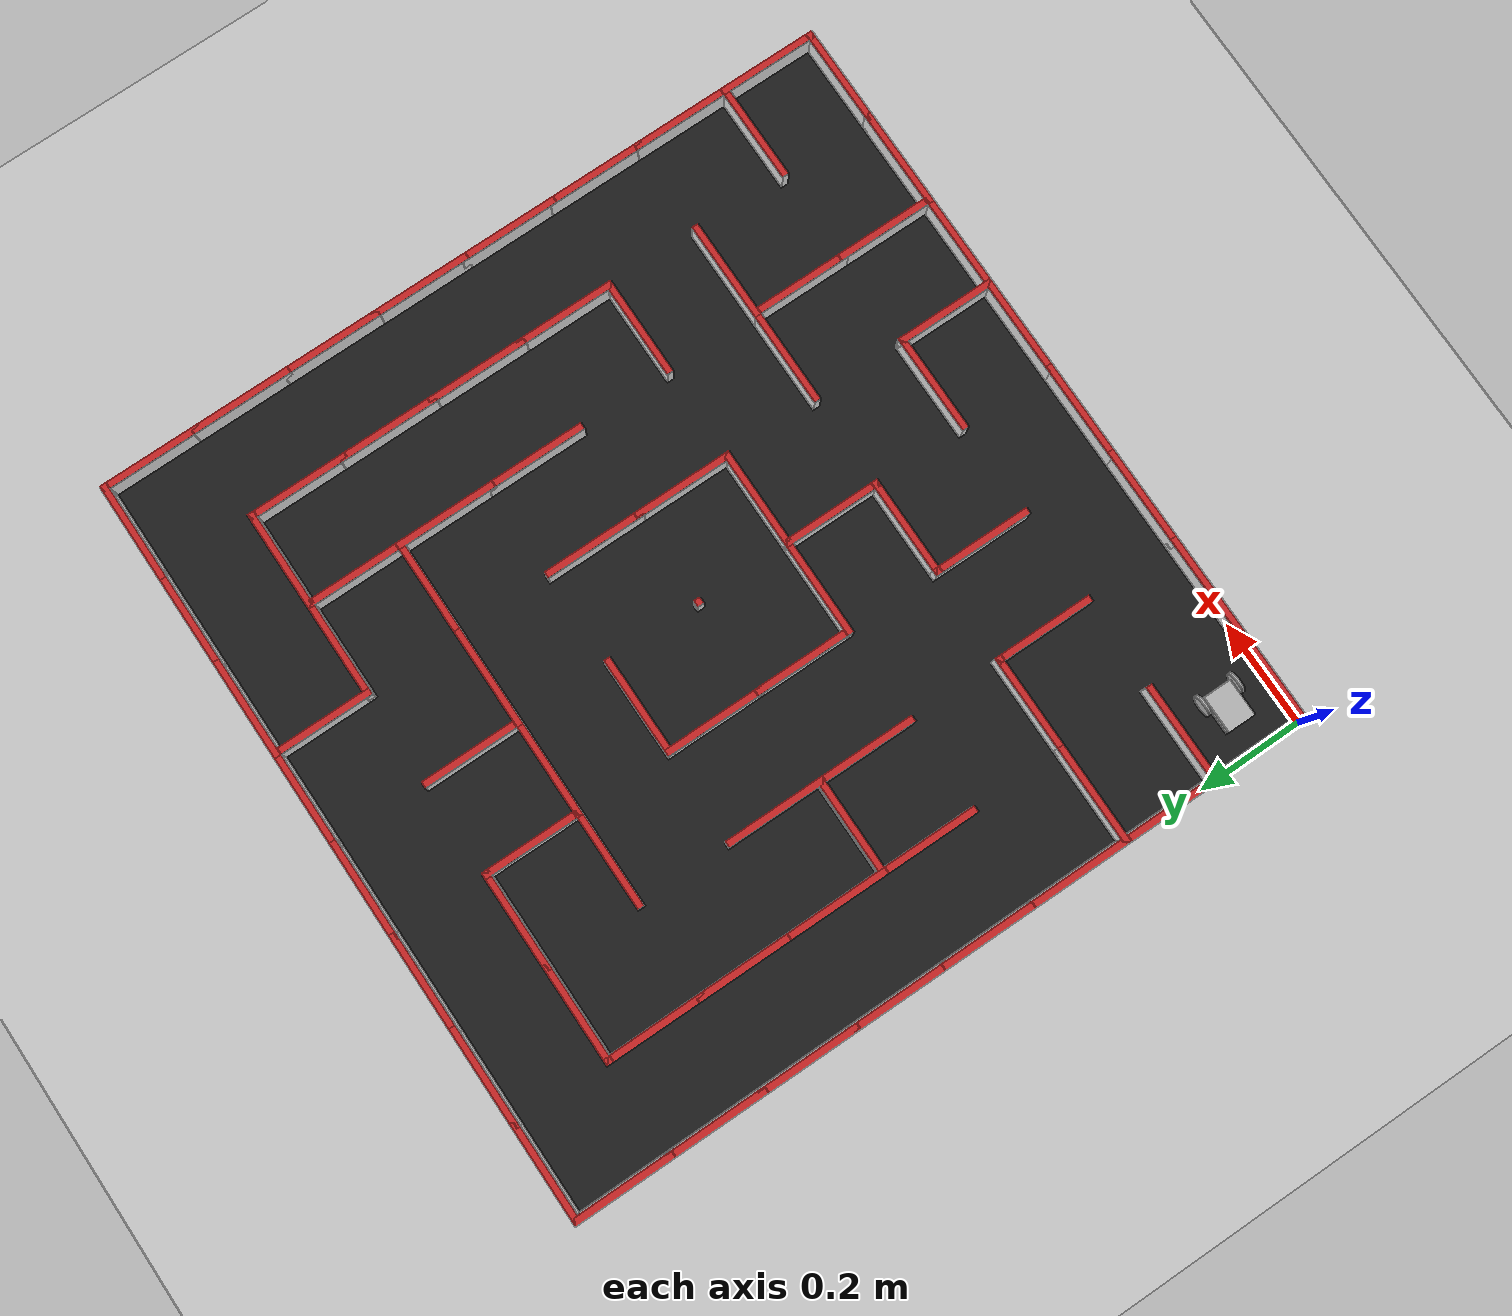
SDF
<?xml version="1.0"?>
<sdf version="1.4">
  <world name="MicroMouse">
    <gui>
      <camera name="user_camera">
        <pose>0.7239 0.7239 2.5 0 1.5707 0</pose>
      </camera>
    </gui>
    <include>
      <uri>model://ground_plane</uri>
    </include>
    <include>
      <uri>model://sun</uri>
    </include>
    <include>
      <uri>model://bot</uri>
      <pose>0.0889 .0889 .0127 0 0 0</pose>
    </include>
    <include>
      <uri>model://easy</uri>
    </include>
  </world>
</sdf>

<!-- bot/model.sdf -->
<sdf version="1.4">
  <model name="remy">
    <static>false</static>
    <plugin name="microbrain" filename="libmicromouse_plugin.so"/>
    <link name="chassis">
      <pose>0 0 .02 0 0 0</pose>
  <inertial>
    <mass>2</mass>
    <inertia>
      <ixx>0</ixx>
      <ixy>1</ixy>
      <ixz>1</ixz>
      <iyy>0</iyy>
      <iyz>0</iyz>
      <izz>0</izz>
    </inertia>
  </inertial>
      <collision name="collision">
        <geometry>
          <box>
            <size>0.07 0.054 .02</size>
          </box>
        </geometry>
      </collision>
      <visual name="visual">
        <geometry>
          <box>
            <size>0.07 0.054 .02</size>
          </box>
        </geometry>
      </visual>
      <collision name="caster_collision">
        <pose>-0.02 0 -0.01 0 0 0</pose>
        <geometry>
          <sphere>
            <radius>.01</radius>
          </sphere>
        </geometry>
        <surface>
          <friction>
            <ode>
              <mu>0</mu>
              <mu2>0</mu2>
              <slip1>1.0</slip1>
              <slip2>1.0</slip2>
            </ode>
          </friction>
        </surface>
      </collision>
      <visual name="caster_visual">
        <pose>-0.02 0 -0.01 0 0 0</pose>
        <geometry>
          <sphere>
            <radius>.01</radius>
          </sphere>
        </geometry>
      </visual>
    </link>
    <link name="sensor">
      <sensor type="ray" name="front">
        <pose>0 0 .06 0 0 0</pose>
        <visualize>true</visualize>
        <update_rate>30</update_rate>
        <always_on>1</always_on>
        <ray>
          <scan>
            <horizontal>
              <samples>30</samples>
              <resolution>1</resolution>
              <min_angle>0.05</min_angle>
              <max_angle>-.05</max_angle>
            </horizontal>
          </scan>
          <range>
            <min>0.02</min>
            <max>0.15</max>
            <resolution>0.001</resolution>
          </range>
          <noise>
            <type>gaussian</type>
            <mean>0.0</mean>
            <stddev>0.001</stddev>
          </noise>
        </ray>
        <plugin name="front_sensor" filename="libgazebo_ros_laser.so">
          <alwaysOn>true</alwaysOn>
          <robotNamespace>remy</robotNamespace>
          <topicName>/sensor/front</topicName>
          <frameName>front</frameName>
        </plugin>
      </sensor>
    </link>
    <link name="left_wheel">
      <pose>0.025 0.034 0.02 0 1.5707 1.5707</pose>
      <collision name="collision">
        <geometry>
          <cylinder>
            <radius>.02</radius>
            <length>.006</length>
          </cylinder>
        </geometry>
      </collision>
      <visual name="visual">
        <geometry>
          <cylinder>
            <radius>.02</radius>
            <length>.006</length>
          </cylinder>
        </geometry>
      </visual>
    </link>
    <link name="right_wheel">
      <pose>0.025 -0.034 0.02 0 1.5707 1.5707</pose>
      <collision name="collision">
        <geometry>
          <cylinder>
            <radius>.02</radius>
            <length>.006</length>
          </cylinder>
        </geometry>
      </collision>
      <visual name="visual">
        <geometry>
          <cylinder>
            <radius>.02</radius>
            <length>.006</length>
          </cylinder>
        </geometry>
      </visual>
    </link>
    <joint type="revolute" name="left_wheel_hinge">
      <pose>0 0 -0.03 0 0 0</pose>
      <child>left_wheel</child>
      <parent>chassis</parent>
      <axis>
        <xyz>0 1 0</xyz>
      </axis>
    </joint>
    <joint type="revolute" name="right_wheel_hinge">
      <pose>0 0 0.03 0 0 0</pose>
      <child>right_wheel</child>
      <parent>chassis</parent>
      <axis>
        <xyz>0 1 0</xyz>
      </axis>
    </joint>
    <plugin name="differential_drive_controller" filename="libgazebo_ros_diff_drive.so">
      <updateRate>1</updateRate>
      <leftJoint>left_wheel_hinge</leftJoint>
      <rightJoint>right_wheel_hinge</rightJoint>
      <wheelSeparation>0.06</wheelSeparation>
      <wheelDiameter>0.04</wheelDiameter>
      <wheelTorque>.5</wheelTorque>
      <commandTopic>cmd_vel</commandTopic>
      <odometryTopic>odom</odometryTopic>
      <odometryFrame>odom</odometryFrame>
      <robotBaseFrame>remy</robotBaseFrame>
      <legacyMode>false</legacyMode>
    </plugin>
  </model>
</sdf>

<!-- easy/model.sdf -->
<sdf version="1.6"><model name="8x8 Maze"><static>1</static><link name="Maze"><collision name="Base_Collision"><pose>0.71755 0.71755 0.00635 0 0 0</pose><geometry><box><size>1.4351 1.4351 0.0127</size></box></geometry>
</collision>
<visual name="Base_Visual"><pose>0.71755 0.71755 0.00635 0 0 0</pose><geometry><box><size>1.4351 1.4351 0.0127</size></box></geometry>
<material><script><uri>file://media/materials/scripts/gazebo.material</uri><name>Gazebo/FlatBlack</name>
</script>
</material>
<meta><layer>0</layer></meta></visual>
<collision name="Post4_4_Collision"><pose>0.71755 0.71755 0.0381 0 0 0</pose><geometry><box><size>0.0127 0.0127 0.0508</size></box></geometry>
</collision>
<visual name="Post4_4_Visual"><pose>0.71755 0.71755 0.0381 0 0 0</pose><geometry><box><size>0.0127 0.0127 0.0498</size></box></geometry>
<material><script><uri>file://media/materials/scripts/gazebo.material</uri><name>Gazebo/White</name>
</script>
</material>
<meta><layer>0</layer></meta></visual>
<visual name="Post4_4_Visual_Cap"><pose>0.71755 0.71755 0.0635 0 0 0</pose><geometry><box><size>0.0127 0.0127 0.001</size></box></geometry>
<material><script><uri>file://media/materials/scripts/gazebo.material</uri><name>Gazebo/Red</name>
</script>
</material>
<meta><layer>0</layer></meta></visual>
<collision name="HWall0_0_Collision"><pose>0.09525 0.00635 0.0381 0 0 0</pose><geometry><box><size>0.1905 0.0127 0.0508</size></box></geometry>
</collision>
<visual name="HWall0_0_Visual"><pose>0.09525 0.00635 0.0381 0 0 0</pose><geometry><box><size>0.1905 0.0127 0.0498</size></box></geometry>
<material><script><uri>file://media/materials/scripts/gazebo.material</uri><name>Gazebo/White</name>
</script>
</material>
<meta><layer>0</layer></meta></visual>
<visual name="HWall0_0_Visual_Cap"><pose>0.09525 0.00635 0.0635 0 0 0</pose><geometry><box><size>0.1905 0.0127 0.001</size></box></geometry>
<material><script><uri>file://media/materials/scripts/gazebo.material</uri><name>Gazebo/Red</name>
</script>
</material>
<meta><layer>0</layer></meta></visual>
<collision name="HWall1_0_Collision"><pose>0.27305 0.00635 0.0381 0 0 0</pose><geometry><box><size>0.1905 0.0127 0.0508</size></box></geometry>
</collision>
<visual name="HWall1_0_Visual"><pose>0.27305 0.00635 0.0381 0 0 0</pose><geometry><box><size>0.1905 0.0127 0.0498</size></box></geometry>
<material><script><uri>file://media/materials/scripts/gazebo.material</uri><name>Gazebo/White</name>
</script>
</material>
<meta><layer>0</layer></meta></visual>
<visual name="HWall1_0_Visual_Cap"><pose>0.27305 0.00635 0.0635 0 0 0</pose><geometry><box><size>0.1905 0.0127 0.001</size></box></geometry>
<material><script><uri>file://media/materials/scripts/gazebo.material</uri><name>Gazebo/Red</name>
</script>
</material>
<meta><layer>0</layer></meta></visual>
<collision name="HWall2_0_Collision"><pose>0.45085 0.00635 0.0381 0 0 0</pose><geometry><box><size>0.1905 0.0127 0.0508</size></box></geometry>
</collision>
<visual name="HWall2_0_Visual"><pose>0.45085 0.00635 0.0381 0 0 0</pose><geometry><box><size>0.1905 0.0127 0.0498</size></box></geometry>
<material><script><uri>file://media/materials/scripts/gazebo.material</uri><name>Gazebo/White</name>
</script>
</material>
<meta><layer>0</layer></meta></visual>
<visual name="HWall2_0_Visual_Cap"><pose>0.45085 0.00635 0.0635 0 0 0</pose><geometry><box><size>0.1905 0.0127 0.001</size></box></geometry>
<material><script><uri>file://media/materials/scripts/gazebo.material</uri><name>Gazebo/Red</name>
</script>
</material>
<meta><layer>0</layer></meta></visual>
<collision name="HWall3_0_Collision"><pose>0.62865 0.00635 0.0381 0 0 0</pose><geometry><box><size>0.1905 0.0127 0.0508</size></box></geometry>
</collision>
<visual name="HWall3_0_Visual"><pose>0.62865 0.00635 0.0381 0 0 0</pose><geometry><box><size>0.1905 0.0127 0.0498</size></box></geometry>
<material><script><uri>file://media/materials/scripts/gazebo.material</uri><name>Gazebo/White</name>
</script>
</material>
<meta><layer>0</layer></meta></visual>
<visual name="HWall3_0_Visual_Cap"><pose>0.62865 0.00635 0.0635 0 0 0</pose><geometry><box><size>0.1905 0.0127 0.001</size></box></geometry>
<material><script><uri>file://media/materials/scripts/gazebo.material</uri><name>Gazebo/Red</name>
</script>
</material>
<meta><layer>0</layer></meta></visual>
<collision name="HWall4_0_Collision"><pose>0.80645 0.00635 0.0381 0 0 0</pose><geometry><box><size>0.1905 0.0127 0.0508</size></box></geometry>
</collision>
<visual name="HWall4_0_Visual"><pose>0.80645 0.00635 0.0381 0 0 0</pose><geometry><box><size>0.1905 0.0127 0.0498</size></box></geometry>
<material><script><uri>file://media/materials/scripts/gazebo.material</uri><name>Gazebo/White</name>
</script>
</material>
<meta><layer>0</layer></meta></visual>
<visual name="HWall4_0_Visual_Cap"><pose>0.80645 0.00635 0.0635 0 0 0</pose><geometry><box><size>0.1905 0.0127 0.001</size></box></geometry>
<material><script><uri>file://media/materials/scripts/gazebo.material</uri><name>Gazebo/Red</name>
</script>
</material>
<meta><layer>0</layer></meta></visual>
<collision name="HWall5_0_Collision"><pose>0.98425 0.00635 0.0381 0 0 0</pose><geometry><box><size>0.1905 0.0127 0.0508</size></box></geometry>
</collision>
<visual name="HWall5_0_Visual"><pose>0.98425 0.00635 0.0381 0 0 0</pose><geometry><box><size>0.1905 0.0127 0.0498</size></box></geometry>
<material><script><uri>file://media/materials/scripts/gazebo.material</uri><name>Gazebo/White</name>
</script>
</material>
<meta><layer>0</layer></meta></visual>
<visual name="HWall5_0_Visual_Cap"><pose>0.98425 0.00635 0.0635 0 0 0</pose><geometry><box><size>0.1905 0.0127 0.001</size></box></geometry>
<material><script><uri>file://media/materials/scripts/gazebo.material</uri><name>Gazebo/Red</name>
</script>
</material>
<meta><layer>0</layer></meta></visual>
<collision name="HWall6_0_Collision"><pose>1.16205 0.00635 0.0381 0 0 0</pose><geometry><box><size>0.1905 0.0127 0.0508</size></box></geometry>
</collision>
<visual name="HWall6_0_Visual"><pose>1.16205 0.00635 0.0381 0 0 0</pose><geometry><box><size>0.1905 0.0127 0.0498</size></box></geometry>
<material><script><uri>file://media/materials/scripts/gazebo.material</uri><name>Gazebo/White</name>
</script>
</material>
<meta><layer>0</layer></meta></visual>
<visual name="HWall6_0_Visual_Cap"><pose>1.16205 0.00635 0.0635 0 0 0</pose><geometry><box><size>0.1905 0.0127 0.001</size></box></geometry>
<material><script><uri>file://media/materials/scripts/gazebo.material</uri><name>Gazebo/Red</name>
</script>
</material>
<meta><layer>0</layer></meta></visual>
<collision name="HWall7_0_Collision"><pose>1.33985 0.00635 0.0381 0 0 0</pose><geometry><box><size>0.1905 0.0127 0.0508</size></box></geometry>
</collision>
<visual name="HWall7_0_Visual"><pose>1.33985 0.00635 0.0381 0 0 0</pose><geometry><box><size>0.1905 0.0127 0.0498</size></box></geometry>
<material><script><uri>file://media/materials/scripts/gazebo.material</uri><name>Gazebo/White</name>
</script>
</material>
<meta><layer>0</layer></meta></visual>
<visual name="HWall7_0_Visual_Cap"><pose>1.33985 0.00635 0.0635 0 0 0</pose><geometry><box><size>0.1905 0.0127 0.001</size></box></geometry>
<material><script><uri>file://media/materials/scripts/gazebo.material</uri><name>Gazebo/Red</name>
</script>
</material>
<meta><layer>0</layer></meta></visual>
<collision name="VWall0_0_Collision"><pose>0.00635 0.09525 0.0381 0 0 0</pose><geometry><box><size>0.0127 0.1905 0.0508</size></box></geometry>
</collision>
<visual name="VWall0_0_Visual"><pose>0.00635 0.09525 0.0381 0 0 0</pose><geometry><box><size>0.0127 0.1905 0.0498</size></box></geometry>
<material><script><uri>file://media/materials/scripts/gazebo.material</uri><name>Gazebo/White</name>
</script>
</material>
<meta><layer>0</layer></meta></visual>
<visual name="VWall0_0_Visual_Cap"><pose>0.00635 0.09525 0.0635 0 0 0</pose><geometry><box><size>0.0127 0.1905 0.001</size></box></geometry>
<material><script><uri>file://media/materials/scripts/gazebo.material</uri><name>Gazebo/Red</name>
</script>
</material>
<meta><layer>0</layer></meta></visual>
<collision name="VWall5_0_Collision"><pose>0.89535 0.09525 0.0381 0 0 0</pose><geometry><box><size>0.0127 0.1905 0.0508</size></box></geometry>
</collision>
<visual name="VWall5_0_Visual"><pose>0.89535 0.09525 0.0381 0 0 0</pose><geometry><box><size>0.0127 0.1905 0.0498</size></box></geometry>
<material><script><uri>file://media/materials/scripts/gazebo.material</uri><name>Gazebo/White</name>
</script>
</material>
<meta><layer>0</layer></meta></visual>
<visual name="VWall5_0_Visual_Cap"><pose>0.89535 0.09525 0.0635 0 0 0</pose><geometry><box><size>0.0127 0.1905 0.001</size></box></geometry>
<material><script><uri>file://media/materials/scripts/gazebo.material</uri><name>Gazebo/Red</name>
</script>
</material>
<meta><layer>0</layer></meta></visual>
<collision name="VWall6_0_Collision"><pose>1.07315 0.09525 0.0381 0 0 0</pose><geometry><box><size>0.0127 0.1905 0.0508</size></box></geometry>
</collision>
<visual name="VWall6_0_Visual"><pose>1.07315 0.09525 0.0381 0 0 0</pose><geometry><box><size>0.0127 0.1905 0.0498</size></box></geometry>
<material><script><uri>file://media/materials/scripts/gazebo.material</uri><name>Gazebo/White</name>
</script>
</material>
<meta><layer>0</layer></meta></visual>
<visual name="VWall6_0_Visual_Cap"><pose>1.07315 0.09525 0.0635 0 0 0</pose><geometry><box><size>0.0127 0.1905 0.001</size></box></geometry>
<material><script><uri>file://media/materials/scripts/gazebo.material</uri><name>Gazebo/Red</name>
</script>
</material>
<meta><layer>0</layer></meta></visual>
<collision name="VWall8_0_Collision"><pose>1.42875 0.09525 0.0381 0 0 0</pose><geometry><box><size>0.0127 0.1905 0.0508</size></box></geometry>
</collision>
<visual name="VWall8_0_Visual"><pose>1.42875 0.09525 0.0381 0 0 0</pose><geometry><box><size>0.0127 0.1905 0.0498</size></box></geometry>
<material><script><uri>file://media/materials/scripts/gazebo.material</uri><name>Gazebo/White</name>
</script>
</material>
<meta><layer>0</layer></meta></visual>
<visual name="VWall8_0_Visual_Cap"><pose>1.42875 0.09525 0.0635 0 0 0</pose><geometry><box><size>0.0127 0.1905 0.001</size></box></geometry>
<material><script><uri>file://media/materials/scripts/gazebo.material</uri><name>Gazebo/Red</name>
</script>
</material>
<meta><layer>0</layer></meta></visual>
<collision name="HWall0_1_Collision"><pose>0.09525 0.18415 0.0381 0 0 0</pose><geometry><box><size>0.1905 0.0127 0.0508</size></box></geometry>
</collision>
<visual name="HWall0_1_Visual"><pose>0.09525 0.18415 0.0381 0 0 0</pose><geometry><box><size>0.1905 0.0127 0.0498</size></box></geometry>
<material><script><uri>file://media/materials/scripts/gazebo.material</uri><name>Gazebo/White</name>
</script>
</material>
<meta><layer>0</layer></meta></visual>
<visual name="HWall0_1_Visual_Cap"><pose>0.09525 0.18415 0.0635 0 0 0</pose><geometry><box><size>0.1905 0.0127 0.001</size></box></geometry>
<material><script><uri>file://media/materials/scripts/gazebo.material</uri><name>Gazebo/Red</name>
</script>
</material>
<meta><layer>0</layer></meta></visual>
<collision name="HWall4_1_Collision"><pose>0.80645 0.18415 0.0381 0 0 0</pose><geometry><box><size>0.1905 0.0127 0.0508</size></box></geometry>
</collision>
<visual name="HWall4_1_Visual"><pose>0.80645 0.18415 0.0381 0 0 0</pose><geometry><box><size>0.1905 0.0127 0.0498</size></box></geometry>
<material><script><uri>file://media/materials/scripts/gazebo.material</uri><name>Gazebo/White</name>
</script>
</material>
<meta><layer>0</layer></meta></visual>
<visual name="HWall4_1_Visual_Cap"><pose>0.80645 0.18415 0.0635 0 0 0</pose><geometry><box><size>0.1905 0.0127 0.001</size></box></geometry>
<material><script><uri>file://media/materials/scripts/gazebo.material</uri><name>Gazebo/Red</name>
</script>
</material>
<meta><layer>0</layer></meta></visual>
<collision name="HWall7_1_Collision"><pose>1.33985 0.18415 0.0381 0 0 0</pose><geometry><box><size>0.1905 0.0127 0.0508</size></box></geometry>
</collision>
<visual name="HWall7_1_Visual"><pose>1.33985 0.18415 0.0381 0 0 0</pose><geometry><box><size>0.1905 0.0127 0.0498</size></box></geometry>
<material><script><uri>file://media/materials/scripts/gazebo.material</uri><name>Gazebo/White</name>
</script>
</material>
<meta><layer>0</layer></meta></visual>
<visual name="HWall7_1_Visual_Cap"><pose>1.33985 0.18415 0.0635 0 0 0</pose><geometry><box><size>0.1905 0.0127 0.001</size></box></geometry>
<material><script><uri>file://media/materials/scripts/gazebo.material</uri><name>Gazebo/Red</name>
</script>
</material>
<meta><layer>0</layer></meta></visual>
<collision name="VWall0_1_Collision"><pose>0.00635 0.27305 0.0381 0 0 0</pose><geometry><box><size>0.0127 0.1905 0.0508</size></box></geometry>
</collision>
<visual name="VWall0_1_Visual"><pose>0.00635 0.27305 0.0381 0 0 0</pose><geometry><box><size>0.0127 0.1905 0.0498</size></box></geometry>
<material><script><uri>file://media/materials/scripts/gazebo.material</uri><name>Gazebo/White</name>
</script>
</material>
<meta><layer>0</layer></meta></visual>
<visual name="VWall0_1_Visual_Cap"><pose>0.00635 0.27305 0.0635 0 0 0</pose><geometry><box><size>0.0127 0.1905 0.001</size></box></geometry>
<material><script><uri>file://media/materials/scripts/gazebo.material</uri><name>Gazebo/Red</name>
</script>
</material>
<meta><layer>0</layer></meta></visual>
<collision name="VWall2_1_Collision"><pose>0.36195 0.27305 0.0381 0 0 0</pose><geometry><box><size>0.0127 0.1905 0.0508</size></box></geometry>
</collision>
<visual name="VWall2_1_Visual"><pose>0.36195 0.27305 0.0381 0 0 0</pose><geometry><box><size>0.0127 0.1905 0.0498</size></box></geometry>
<material><script><uri>file://media/materials/scripts/gazebo.material</uri><name>Gazebo/White</name>
</script>
</material>
<meta><layer>0</layer></meta></visual>
<visual name="VWall2_1_Visual_Cap"><pose>0.36195 0.27305 0.0635 0 0 0</pose><geometry><box><size>0.0127 0.1905 0.001</size></box></geometry>
<material><script><uri>file://media/materials/scripts/gazebo.material</uri><name>Gazebo/Red</name>
</script>
</material>
<meta><layer>0</layer></meta></visual>
<collision name="VWall3_1_Collision"><pose>0.53975 0.27305 0.0381 0 0 0</pose><geometry><box><size>0.0127 0.1905 0.0508</size></box></geometry>
</collision>
<visual name="VWall3_1_Visual"><pose>0.53975 0.27305 0.0381 0 0 0</pose><geometry><box><size>0.0127 0.1905 0.0498</size></box></geometry>
<material><script><uri>file://media/materials/scripts/gazebo.material</uri><name>Gazebo/White</name>
</script>
</material>
<meta><layer>0</layer></meta></visual>
<visual name="VWall3_1_Visual_Cap"><pose>0.53975 0.27305 0.0635 0 0 0</pose><geometry><box><size>0.0127 0.1905 0.001</size></box></geometry>
<material><script><uri>file://media/materials/scripts/gazebo.material</uri><name>Gazebo/Red</name>
</script>
</material>
<meta><layer>0</layer></meta></visual>
<collision name="VWall6_1_Collision"><pose>1.07315 0.27305 0.0381 0 0 0</pose><geometry><box><size>0.0127 0.1905 0.0508</size></box></geometry>
</collision>
<visual name="VWall6_1_Visual"><pose>1.07315 0.27305 0.0381 0 0 0</pose><geometry><box><size>0.0127 0.1905 0.0498</size></box></geometry>
<material><script><uri>file://media/materials/scripts/gazebo.material</uri><name>Gazebo/White</name>
</script>
</material>
<meta><layer>0</layer></meta></visual>
<visual name="VWall6_1_Visual_Cap"><pose>1.07315 0.27305 0.0635 0 0 0</pose><geometry><box><size>0.0127 0.1905 0.001</size></box></geometry>
<material><script><uri>file://media/materials/scripts/gazebo.material</uri><name>Gazebo/Red</name>
</script>
</material>
<meta><layer>0</layer></meta></visual>
<collision name="VWall8_1_Collision"><pose>1.42875 0.27305 0.0381 0 0 0</pose><geometry><box><size>0.0127 0.1905 0.0508</size></box></geometry>
</collision>
<visual name="VWall8_1_Visual"><pose>1.42875 0.27305 0.0381 0 0 0</pose><geometry><box><size>0.0127 0.1905 0.0498</size></box></geometry>
<material><script><uri>file://media/materials/scripts/gazebo.material</uri><name>Gazebo/White</name>
</script>
</material>
<meta><layer>0</layer></meta></visual>
<visual name="VWall8_1_Visual_Cap"><pose>1.42875 0.27305 0.0635 0 0 0</pose><geometry><box><size>0.0127 0.1905 0.001</size></box></geometry>
<material><script><uri>file://media/materials/scripts/gazebo.material</uri><name>Gazebo/Red</name>
</script>
</material>
<meta><layer>0</layer></meta></visual>
<collision name="HWall0_2_Collision"><pose>0.09525 0.36195 0.0381 0 0 0</pose><geometry><box><size>0.1905 0.0127 0.0508</size></box></geometry>
</collision>
<visual name="HWall0_2_Visual"><pose>0.09525 0.36195 0.0381 0 0 0</pose><geometry><box><size>0.1905 0.0127 0.0498</size></box></geometry>
<material><script><uri>file://media/materials/scripts/gazebo.material</uri><name>Gazebo/White</name>
</script>
</material>
<meta><layer>0</layer></meta></visual>
<visual name="HWall0_2_Visual_Cap"><pose>0.09525 0.36195 0.0635 0 0 0</pose><geometry><box><size>0.1905 0.0127 0.001</size></box></geometry>
<material><script><uri>file://media/materials/scripts/gazebo.material</uri><name>Gazebo/Red</name>
</script>
</material>
<meta><layer>0</layer></meta></visual>
<collision name="HWall1_2_Collision"><pose>0.27305 0.36195 0.0381 0 0 0</pose><geometry><box><size>0.1905 0.0127 0.0508</size></box></geometry>
</collision>
<visual name="HWall1_2_Visual"><pose>0.27305 0.36195 0.0381 0 0 0</pose><geometry><box><size>0.1905 0.0127 0.0498</size></box></geometry>
<material><script><uri>file://media/materials/scripts/gazebo.material</uri><name>Gazebo/White</name>
</script>
</material>
<meta><layer>0</layer></meta></visual>
<visual name="HWall1_2_Visual_Cap"><pose>0.27305 0.36195 0.0635 0 0 0</pose><geometry><box><size>0.1905 0.0127 0.001</size></box></geometry>
<material><script><uri>file://media/materials/scripts/gazebo.material</uri><name>Gazebo/Red</name>
</script>
</material>
<meta><layer>0</layer></meta></visual>
<collision name="HWall3_2_Collision"><pose>0.62865 0.36195 0.0381 0 0 0</pose><geometry><box><size>0.1905 0.0127 0.0508</size></box></geometry>
</collision>
<visual name="HWall3_2_Visual"><pose>0.62865 0.36195 0.0381 0 0 0</pose><geometry><box><size>0.1905 0.0127 0.0498</size></box></geometry>
<material><script><uri>file://media/materials/scripts/gazebo.material</uri><name>Gazebo/White</name>
</script>
</material>
<meta><layer>0</layer></meta></visual>
<visual name="HWall3_2_Visual_Cap"><pose>0.62865 0.36195 0.0635 0 0 0</pose><geometry><box><size>0.1905 0.0127 0.001</size></box></geometry>
<material><script><uri>file://media/materials/scripts/gazebo.material</uri><name>Gazebo/Red</name>
</script>
</material>
<meta><layer>0</layer></meta></visual>
<collision name="HWall5_2_Collision"><pose>0.98425 0.36195 0.0381 0 0 0</pose><geometry><box><size>0.1905 0.0127 0.0508</size></box></geometry>
</collision>
<visual name="HWall5_2_Visual"><pose>0.98425 0.36195 0.0381 0 0 0</pose><geometry><box><size>0.1905 0.0127 0.0498</size></box></geometry>
<material><script><uri>file://media/materials/scripts/gazebo.material</uri><name>Gazebo/White</name>
</script>
</material>
<meta><layer>0</layer></meta></visual>
<visual name="HWall5_2_Visual_Cap"><pose>0.98425 0.36195 0.0635 0 0 0</pose><geometry><box><size>0.1905 0.0127 0.001</size></box></geometry>
<material><script><uri>file://media/materials/scripts/gazebo.material</uri><name>Gazebo/Red</name>
</script>
</material>
<meta><layer>0</layer></meta></visual>
<collision name="HWall6_2_Collision"><pose>1.16205 0.36195 0.0381 0 0 0</pose><geometry><box><size>0.1905 0.0127 0.0508</size></box></geometry>
</collision>
<visual name="HWall6_2_Visual"><pose>1.16205 0.36195 0.0381 0 0 0</pose><geometry><box><size>0.1905 0.0127 0.0498</size></box></geometry>
<material><script><uri>file://media/materials/scripts/gazebo.material</uri><name>Gazebo/White</name>
</script>
</material>
<meta><layer>0</layer></meta></visual>
<visual name="HWall6_2_Visual_Cap"><pose>1.16205 0.36195 0.0635 0 0 0</pose><geometry><box><size>0.1905 0.0127 0.001</size></box></geometry>
<material><script><uri>file://media/materials/scripts/gazebo.material</uri><name>Gazebo/Red</name>
</script>
</material>
<meta><layer>0</layer></meta></visual>
<collision name="VWall0_2_Collision"><pose>0.00635 0.45085 0.0381 0 0 0</pose><geometry><box><size>0.0127 0.1905 0.0508</size></box></geometry>
</collision>
<visual name="VWall0_2_Visual"><pose>0.00635 0.45085 0.0381 0 0 0</pose><geometry><box><size>0.0127 0.1905 0.0498</size></box></geometry>
<material><script><uri>file://media/materials/scripts/gazebo.material</uri><name>Gazebo/White</name>
</script>
</material>
<meta><layer>0</layer></meta></visual>
<visual name="VWall0_2_Visual_Cap"><pose>0.00635 0.45085 0.0635 0 0 0</pose><geometry><box><size>0.0127 0.1905 0.001</size></box></geometry>
<material><script><uri>file://media/materials/scripts/gazebo.material</uri><name>Gazebo/Red</name>
</script>
</material>
<meta><layer>0</layer></meta></visual>
<collision name="VWall4_2_Collision"><pose>0.71755 0.45085 0.0381 0 0 0</pose><geometry><box><size>0.0127 0.1905 0.0508</size></box></geometry>
</collision>
<visual name="VWall4_2_Visual"><pose>0.71755 0.45085 0.0381 0 0 0</pose><geometry><box><size>0.0127 0.1905 0.0498</size></box></geometry>
<material><script><uri>file://media/materials/scripts/gazebo.material</uri><name>Gazebo/White</name>
</script>
</material>
<meta><layer>0</layer></meta></visual>
<visual name="VWall4_2_Visual_Cap"><pose>0.71755 0.45085 0.0635 0 0 0</pose><geometry><box><size>0.0127 0.1905 0.001</size></box></geometry>
<material><script><uri>file://media/materials/scripts/gazebo.material</uri><name>Gazebo/Red</name>
</script>
</material>
<meta><layer>0</layer></meta></visual>
<collision name="VWall8_2_Collision"><pose>1.42875 0.45085 0.0381 0 0 0</pose><geometry><box><size>0.0127 0.1905 0.0508</size></box></geometry>
</collision>
<visual name="VWall8_2_Visual"><pose>1.42875 0.45085 0.0381 0 0 0</pose><geometry><box><size>0.0127 0.1905 0.0498</size></box></geometry>
<material><script><uri>file://media/materials/scripts/gazebo.material</uri><name>Gazebo/White</name>
</script>
</material>
<meta><layer>0</layer></meta></visual>
<visual name="VWall8_2_Visual_Cap"><pose>1.42875 0.45085 0.0635 0 0 0</pose><geometry><box><size>0.0127 0.1905 0.001</size></box></geometry>
<material><script><uri>file://media/materials/scripts/gazebo.material</uri><name>Gazebo/Red</name>
</script>
</material>
<meta><layer>0</layer></meta></visual>
<collision name="HWall3_3_Collision"><pose>0.62865 0.53975 0.0381 0 0 0</pose><geometry><box><size>0.1905 0.0127 0.0508</size></box></geometry>
</collision>
<visual name="HWall3_3_Visual"><pose>0.62865 0.53975 0.0381 0 0 0</pose><geometry><box><size>0.1905 0.0127 0.0498</size></box></geometry>
<material><script><uri>file://media/materials/scripts/gazebo.material</uri><name>Gazebo/White</name>
</script>
</material>
<meta><layer>0</layer></meta></visual>
<visual name="HWall3_3_Visual_Cap"><pose>0.62865 0.53975 0.0635 0 0 0</pose><geometry><box><size>0.1905 0.0127 0.001</size></box></geometry>
<material><script><uri>file://media/materials/scripts/gazebo.material</uri><name>Gazebo/Red</name>
</script>
</material>
<meta><layer>0</layer></meta></visual>
<collision name="HWall4_3_Collision"><pose>0.80645 0.53975 0.0381 0 0 0</pose><geometry><box><size>0.1905 0.0127 0.0508</size></box></geometry>
</collision>
<visual name="HWall4_3_Visual"><pose>0.80645 0.53975 0.0381 0 0 0</pose><geometry><box><size>0.1905 0.0127 0.0498</size></box></geometry>
<material><script><uri>file://media/materials/scripts/gazebo.material</uri><name>Gazebo/White</name>
</script>
</material>
<meta><layer>0</layer></meta></visual>
<visual name="HWall4_3_Visual_Cap"><pose>0.80645 0.53975 0.0635 0 0 0</pose><geometry><box><size>0.1905 0.0127 0.001</size></box></geometry>
<material><script><uri>file://media/materials/scripts/gazebo.material</uri><name>Gazebo/Red</name>
</script>
</material>
<meta><layer>0</layer></meta></visual>
<collision name="HWall6_3_Collision"><pose>1.16205 0.53975 0.0381 0 0 0</pose><geometry><box><size>0.1905 0.0127 0.0508</size></box></geometry>
</collision>
<visual name="HWall6_3_Visual"><pose>1.16205 0.53975 0.0381 0 0 0</pose><geometry><box><size>0.1905 0.0127 0.0498</size></box></geometry>
<material><script><uri>file://media/materials/scripts/gazebo.material</uri><name>Gazebo/White</name>
</script>
</material>
<meta><layer>0</layer></meta></visual>
<visual name="HWall6_3_Visual_Cap"><pose>1.16205 0.53975 0.0635 0 0 0</pose><geometry><box><size>0.1905 0.0127 0.001</size></box></geometry>
<material><script><uri>file://media/materials/scripts/gazebo.material</uri><name>Gazebo/Red</name>
</script>
</material>
<meta><layer>0</layer></meta></visual>
<collision name="VWall0_3_Collision"><pose>0.00635 0.62865 0.0381 0 0 0</pose><geometry><box><size>0.0127 0.1905 0.0508</size></box></geometry>
</collision>
<visual name="VWall0_3_Visual"><pose>0.00635 0.62865 0.0381 0 0 0</pose><geometry><box><size>0.0127 0.1905 0.0498</size></box></geometry>
<material><script><uri>file://media/materials/scripts/gazebo.material</uri><name>Gazebo/White</name>
</script>
</material>
<meta><layer>0</layer></meta></visual>
<visual name="VWall0_3_Visual_Cap"><pose>0.00635 0.62865 0.0635 0 0 0</pose><geometry><box><size>0.0127 0.1905 0.001</size></box></geometry>
<material><script><uri>file://media/materials/scripts/gazebo.material</uri><name>Gazebo/Red</name>
</script>
</material>
<meta><layer>0</layer></meta></visual>
<collision name="VWall1_3_Collision"><pose>0.18415 0.62865 0.0381 0 0 0</pose><geometry><box><size>0.0127 0.1905 0.0508</size></box></geometry>
</collision>
<visual name="VWall1_3_Visual"><pose>0.18415 0.62865 0.0381 0 0 0</pose><geometry><box><size>0.0127 0.1905 0.0498</size></box></geometry>
<material><script><uri>file://media/materials/scripts/gazebo.material</uri><name>Gazebo/White</name>
</script>
</material>
<meta><layer>0</layer></meta></visual>
<visual name="VWall1_3_Visual_Cap"><pose>0.18415 0.62865 0.0635 0 0 0</pose><geometry><box><size>0.0127 0.1905 0.001</size></box></geometry>
<material><script><uri>file://media/materials/scripts/gazebo.material</uri><name>Gazebo/Red</name>
</script>
</material>
<meta><layer>0</layer></meta></visual>
<collision name="VWall2_3_Collision"><pose>0.36195 0.62865 0.0381 0 0 0</pose><geometry><box><size>0.0127 0.1905 0.0508</size></box></geometry>
</collision>
<visual name="VWall2_3_Visual"><pose>0.36195 0.62865 0.0381 0 0 0</pose><geometry><box><size>0.0127 0.1905 0.0498</size></box></geometry>
<material><script><uri>file://media/materials/scripts/gazebo.material</uri><name>Gazebo/White</name>
</script>
</material>
<meta><layer>0</layer></meta></visual>
<visual name="VWall2_3_Visual_Cap"><pose>0.36195 0.62865 0.0635 0 0 0</pose><geometry><box><size>0.0127 0.1905 0.001</size></box></geometry>
<material><script><uri>file://media/materials/scripts/gazebo.material</uri><name>Gazebo/Red</name>
</script>
</material>
<meta><layer>0</layer></meta></visual>
<collision name="VWall3_3_Collision"><pose>0.53975 0.62865 0.0381 0 0 0</pose><geometry><box><size>0.0127 0.1905 0.0508</size></box></geometry>
</collision>
<visual name="VWall3_3_Visual"><pose>0.53975 0.62865 0.0381 0 0 0</pose><geometry><box><size>0.0127 0.1905 0.0498</size></box></geometry>
<material><script><uri>file://media/materials/scripts/gazebo.material</uri><name>Gazebo/White</name>
</script>
</material>
<meta><layer>0</layer></meta></visual>
<visual name="VWall3_3_Visual_Cap"><pose>0.53975 0.62865 0.0635 0 0 0</pose><geometry><box><size>0.0127 0.1905 0.001</size></box></geometry>
<material><script><uri>file://media/materials/scripts/gazebo.material</uri><name>Gazebo/Red</name>
</script>
</material>
<meta><layer>0</layer></meta></visual>
<collision name="VWall5_3_Collision"><pose>0.89535 0.62865 0.0381 0 0 0</pose><geometry><box><size>0.0127 0.1905 0.0508</size></box></geometry>
</collision>
<visual name="VWall5_3_Visual"><pose>0.89535 0.62865 0.0381 0 0 0</pose><geometry><box><size>0.0127 0.1905 0.0498</size></box></geometry>
<material><script><uri>file://media/materials/scripts/gazebo.material</uri><name>Gazebo/White</name>
</script>
</material>
<meta><layer>0</layer></meta></visual>
<visual name="VWall5_3_Visual_Cap"><pose>0.89535 0.62865 0.0635 0 0 0</pose><geometry><box><size>0.0127 0.1905 0.001</size></box></geometry>
<material><script><uri>file://media/materials/scripts/gazebo.material</uri><name>Gazebo/Red</name>
</script>
</material>
<meta><layer>0</layer></meta></visual>
<collision name="VWall7_3_Collision"><pose>1.25095 0.62865 0.0381 0 0 0</pose><geometry><box><size>0.0127 0.1905 0.0508</size></box></geometry>
</collision>
<visual name="VWall7_3_Visual"><pose>1.25095 0.62865 0.0381 0 0 0</pose><geometry><box><size>0.0127 0.1905 0.0498</size></box></geometry>
<material><script><uri>file://media/materials/scripts/gazebo.material</uri><name>Gazebo/White</name>
</script>
</material>
<meta><layer>0</layer></meta></visual>
<visual name="VWall7_3_Visual_Cap"><pose>1.25095 0.62865 0.0635 0 0 0</pose><geometry><box><size>0.0127 0.1905 0.001</size></box></geometry>
<material><script><uri>file://media/materials/scripts/gazebo.material</uri><name>Gazebo/Red</name>
</script>
</material>
<meta><layer>0</layer></meta></visual>
<collision name="VWall8_3_Collision"><pose>1.42875 0.62865 0.0381 0 0 0</pose><geometry><box><size>0.0127 0.1905 0.0508</size></box></geometry>
</collision>
<visual name="VWall8_3_Visual"><pose>1.42875 0.62865 0.0381 0 0 0</pose><geometry><box><size>0.0127 0.1905 0.0498</size></box></geometry>
<material><script><uri>file://media/materials/scripts/gazebo.material</uri><name>Gazebo/White</name>
</script>
</material>
<meta><layer>0</layer></meta></visual>
<visual name="VWall8_3_Visual_Cap"><pose>1.42875 0.62865 0.0635 0 0 0</pose><geometry><box><size>0.0127 0.1905 0.001</size></box></geometry>
<material><script><uri>file://media/materials/scripts/gazebo.material</uri><name>Gazebo/Red</name>
</script>
</material>
<meta><layer>0</layer></meta></visual>
<collision name="HWall1_4_Collision"><pose>0.27305 0.71755 0.0381 0 0 0</pose><geometry><box><size>0.1905 0.0127 0.0508</size></box></geometry>
</collision>
<visual name="HWall1_4_Visual"><pose>0.27305 0.71755 0.0381 0 0 0</pose><geometry><box><size>0.1905 0.0127 0.0498</size></box></geometry>
<material><script><uri>file://media/materials/scripts/gazebo.material</uri><name>Gazebo/White</name>
</script>
</material>
<meta><layer>0</layer></meta></visual>
<visual name="HWall1_4_Visual_Cap"><pose>0.27305 0.71755 0.0635 0 0 0</pose><geometry><box><size>0.1905 0.0127 0.001</size></box></geometry>
<material><script><uri>file://media/materials/scripts/gazebo.material</uri><name>Gazebo/Red</name>
</script>
</material>
<meta><layer>0</layer></meta></visual>
<collision name="VWall0_4_Collision"><pose>0.00635 0.80645 0.0381 0 0 0</pose><geometry><box><size>0.0127 0.1905 0.0508</size></box></geometry>
</collision>
<visual name="VWall0_4_Visual"><pose>0.00635 0.80645 0.0381 0 0 0</pose><geometry><box><size>0.0127 0.1905 0.0498</size></box></geometry>
<material><script><uri>file://media/materials/scripts/gazebo.material</uri><name>Gazebo/White</name>
</script>
</material>
<meta><layer>0</layer></meta></visual>
<visual name="VWall0_4_Visual_Cap"><pose>0.00635 0.80645 0.0635 0 0 0</pose><geometry><box><size>0.0127 0.1905 0.001</size></box></geometry>
<material><script><uri>file://media/materials/scripts/gazebo.material</uri><name>Gazebo/Red</name>
</script>
</material>
<meta><layer>0</layer></meta></visual>
<collision name="VWall1_4_Collision"><pose>0.18415 0.80645 0.0381 0 0 0</pose><geometry><box><size>0.0127 0.1905 0.0508</size></box></geometry>
</collision>
<visual name="VWall1_4_Visual"><pose>0.18415 0.80645 0.0381 0 0 0</pose><geometry><box><size>0.0127 0.1905 0.0498</size></box></geometry>
<material><script><uri>file://media/materials/scripts/gazebo.material</uri><name>Gazebo/White</name>
</script>
</material>
<meta><layer>0</layer></meta></visual>
<visual name="VWall1_4_Visual_Cap"><pose>0.18415 0.80645 0.0635 0 0 0</pose><geometry><box><size>0.0127 0.1905 0.001</size></box></geometry>
<material><script><uri>file://media/materials/scripts/gazebo.material</uri><name>Gazebo/Red</name>
</script>
</material>
<meta><layer>0</layer></meta></visual>
<collision name="VWall2_4_Collision"><pose>0.36195 0.80645 0.0381 0 0 0</pose><geometry><box><size>0.0127 0.1905 0.0508</size></box></geometry>
</collision>
<visual name="VWall2_4_Visual"><pose>0.36195 0.80645 0.0381 0 0 0</pose><geometry><box><size>0.0127 0.1905 0.0498</size></box></geometry>
<material><script><uri>file://media/materials/scripts/gazebo.material</uri><name>Gazebo/White</name>
</script>
</material>
<meta><layer>0</layer></meta></visual>
<visual name="VWall2_4_Visual_Cap"><pose>0.36195 0.80645 0.0635 0 0 0</pose><geometry><box><size>0.0127 0.1905 0.001</size></box></geometry>
<material><script><uri>file://media/materials/scripts/gazebo.material</uri><name>Gazebo/Red</name>
</script>
</material>
<meta><layer>0</layer></meta></visual>
<collision name="VWall3_4_Collision"><pose>0.53975 0.80645 0.0381 0 0 0</pose><geometry><box><size>0.0127 0.1905 0.0508</size></box></geometry>
</collision>
<visual name="VWall3_4_Visual"><pose>0.53975 0.80645 0.0381 0 0 0</pose><geometry><box><size>0.0127 0.1905 0.0498</size></box></geometry>
<material><script><uri>file://media/materials/scripts/gazebo.material</uri><name>Gazebo/White</name>
</script>
</material>
<meta><layer>0</layer></meta></visual>
<visual name="VWall3_4_Visual_Cap"><pose>0.53975 0.80645 0.0635 0 0 0</pose><geometry><box><size>0.0127 0.1905 0.001</size></box></geometry>
<material><script><uri>file://media/materials/scripts/gazebo.material</uri><name>Gazebo/Red</name>
</script>
</material>
<meta><layer>0</layer></meta></visual>
<collision name="VWall5_4_Collision"><pose>0.89535 0.80645 0.0381 0 0 0</pose><geometry><box><size>0.0127 0.1905 0.0508</size></box></geometry>
</collision>
<visual name="VWall5_4_Visual"><pose>0.89535 0.80645 0.0381 0 0 0</pose><geometry><box><size>0.0127 0.1905 0.0498</size></box></geometry>
<material><script><uri>file://media/materials/scripts/gazebo.material</uri><name>Gazebo/White</name>
</script>
</material>
<meta><layer>0</layer></meta></visual>
<visual name="VWall5_4_Visual_Cap"><pose>0.89535 0.80645 0.0635 0 0 0</pose><geometry><box><size>0.0127 0.1905 0.001</size></box></geometry>
<material><script><uri>file://media/materials/scripts/gazebo.material</uri><name>Gazebo/Red</name>
</script>
</material>
<meta><layer>0</layer></meta></visual>
<collision name="VWall6_4_Collision"><pose>1.07315 0.80645 0.0381 0 0 0</pose><geometry><box><size>0.0127 0.1905 0.0508</size></box></geometry>
</collision>
<visual name="VWall6_4_Visual"><pose>1.07315 0.80645 0.0381 0 0 0</pose><geometry><box><size>0.0127 0.1905 0.0498</size></box></geometry>
<material><script><uri>file://media/materials/scripts/gazebo.material</uri><name>Gazebo/White</name>
</script>
</material>
<meta><layer>0</layer></meta></visual>
<visual name="VWall6_4_Visual_Cap"><pose>1.07315 0.80645 0.0635 0 0 0</pose><geometry><box><size>0.0127 0.1905 0.001</size></box></geometry>
<material><script><uri>file://media/materials/scripts/gazebo.material</uri><name>Gazebo/Red</name>
</script>
</material>
<meta><layer>0</layer></meta></visual>
<collision name="VWall7_4_Collision"><pose>1.25095 0.80645 0.0381 0 0 0</pose><geometry><box><size>0.0127 0.1905 0.0508</size></box></geometry>
</collision>
<visual name="VWall7_4_Visual"><pose>1.25095 0.80645 0.0381 0 0 0</pose><geometry><box><size>0.0127 0.1905 0.0498</size></box></geometry>
<material><script><uri>file://media/materials/scripts/gazebo.material</uri><name>Gazebo/White</name>
</script>
</material>
<meta><layer>0</layer></meta></visual>
<visual name="VWall7_4_Visual_Cap"><pose>1.25095 0.80645 0.0635 0 0 0</pose><geometry><box><size>0.0127 0.1905 0.001</size></box></geometry>
<material><script><uri>file://media/materials/scripts/gazebo.material</uri><name>Gazebo/Red</name>
</script>
</material>
<meta><layer>0</layer></meta></visual>
<collision name="VWall8_4_Collision"><pose>1.42875 0.80645 0.0381 0 0 0</pose><geometry><box><size>0.0127 0.1905 0.0508</size></box></geometry>
</collision>
<visual name="VWall8_4_Visual"><pose>1.42875 0.80645 0.0381 0 0 0</pose><geometry><box><size>0.0127 0.1905 0.0498</size></box></geometry>
<material><script><uri>file://media/materials/scripts/gazebo.material</uri><name>Gazebo/White</name>
</script>
</material>
<meta><layer>0</layer></meta></visual>
<visual name="VWall8_4_Visual_Cap"><pose>1.42875 0.80645 0.0635 0 0 0</pose><geometry><box><size>0.0127 0.1905 0.001</size></box></geometry>
<material><script><uri>file://media/materials/scripts/gazebo.material</uri><name>Gazebo/Red</name>
</script>
</material>
<meta><layer>0</layer></meta></visual>
<collision name="HWall3_5_Collision"><pose>0.62865 0.89535 0.0381 0 0 0</pose><geometry><box><size>0.1905 0.0127 0.0508</size></box></geometry>
</collision>
<visual name="HWall3_5_Visual"><pose>0.62865 0.89535 0.0381 0 0 0</pose><geometry><box><size>0.1905 0.0127 0.0498</size></box></geometry>
<material><script><uri>file://media/materials/scripts/gazebo.material</uri><name>Gazebo/White</name>
</script>
</material>
<meta><layer>0</layer></meta></visual>
<visual name="HWall3_5_Visual_Cap"><pose>0.62865 0.89535 0.0635 0 0 0</pose><geometry><box><size>0.1905 0.0127 0.001</size></box></geometry>
<material><script><uri>file://media/materials/scripts/gazebo.material</uri><name>Gazebo/Red</name>
</script>
</material>
<meta><layer>0</layer></meta></visual>
<collision name="VWall0_5_Collision"><pose>0.00635 0.98425 0.0381 0 0 0</pose><geometry><box><size>0.0127 0.1905 0.0508</size></box></geometry>
</collision>
<visual name="VWall0_5_Visual"><pose>0.00635 0.98425 0.0381 0 0 0</pose><geometry><box><size>0.0127 0.1905 0.0498</size></box></geometry>
<material><script><uri>file://media/materials/scripts/gazebo.material</uri><name>Gazebo/White</name>
</script>
</material>
<meta><layer>0</layer></meta></visual>
<visual name="VWall0_5_Visual_Cap"><pose>0.00635 0.98425 0.0635 0 0 0</pose><geometry><box><size>0.0127 0.1905 0.001</size></box></geometry>
<material><script><uri>file://media/materials/scripts/gazebo.material</uri><name>Gazebo/Red</name>
</script>
</material>
<meta><layer>0</layer></meta></visual>
<collision name="VWall1_5_Collision"><pose>0.18415 0.98425 0.0381 0 0 0</pose><geometry><box><size>0.0127 0.1905 0.0508</size></box></geometry>
</collision>
<visual name="VWall1_5_Visual"><pose>0.18415 0.98425 0.0381 0 0 0</pose><geometry><box><size>0.0127 0.1905 0.0498</size></box></geometry>
<material><script><uri>file://media/materials/scripts/gazebo.material</uri><name>Gazebo/White</name>
</script>
</material>
<meta><layer>0</layer></meta></visual>
<visual name="VWall1_5_Visual_Cap"><pose>0.18415 0.98425 0.0635 0 0 0</pose><geometry><box><size>0.0127 0.1905 0.001</size></box></geometry>
<material><script><uri>file://media/materials/scripts/gazebo.material</uri><name>Gazebo/Red</name>
</script>
</material>
<meta><layer>0</layer></meta></visual>
<collision name="VWall6_5_Collision"><pose>1.07315 0.98425 0.0381 0 0 0</pose><geometry><box><size>0.0127 0.1905 0.0508</size></box></geometry>
</collision>
<visual name="VWall6_5_Visual"><pose>1.07315 0.98425 0.0381 0 0 0</pose><geometry><box><size>0.0127 0.1905 0.0498</size></box></geometry>
<material><script><uri>file://media/materials/scripts/gazebo.material</uri><name>Gazebo/White</name>
</script>
</material>
<meta><layer>0</layer></meta></visual>
<visual name="VWall6_5_Visual_Cap"><pose>1.07315 0.98425 0.0635 0 0 0</pose><geometry><box><size>0.0127 0.1905 0.001</size></box></geometry>
<material><script><uri>file://media/materials/scripts/gazebo.material</uri><name>Gazebo/Red</name>
</script>
</material>
<meta><layer>0</layer></meta></visual>
<collision name="VWall7_5_Collision"><pose>1.25095 0.98425 0.0381 0 0 0</pose><geometry><box><size>0.0127 0.1905 0.0508</size></box></geometry>
</collision>
<visual name="VWall7_5_Visual"><pose>1.25095 0.98425 0.0381 0 0 0</pose><geometry><box><size>0.0127 0.1905 0.0498</size></box></geometry>
<material><script><uri>file://media/materials/scripts/gazebo.material</uri><name>Gazebo/White</name>
</script>
</material>
<meta><layer>0</layer></meta></visual>
<visual name="VWall7_5_Visual_Cap"><pose>1.25095 0.98425 0.0635 0 0 0</pose><geometry><box><size>0.0127 0.1905 0.001</size></box></geometry>
<material><script><uri>file://media/materials/scripts/gazebo.material</uri><name>Gazebo/Red</name>
</script>
</material>
<meta><layer>0</layer></meta></visual>
<collision name="VWall8_5_Collision"><pose>1.42875 0.98425 0.0381 0 0 0</pose><geometry><box><size>0.0127 0.1905 0.0508</size></box></geometry>
</collision>
<visual name="VWall8_5_Visual"><pose>1.42875 0.98425 0.0381 0 0 0</pose><geometry><box><size>0.0127 0.1905 0.0498</size></box></geometry>
<material><script><uri>file://media/materials/scripts/gazebo.material</uri><name>Gazebo/White</name>
</script>
</material>
<meta><layer>0</layer></meta></visual>
<visual name="VWall8_5_Visual_Cap"><pose>1.42875 0.98425 0.0635 0 0 0</pose><geometry><box><size>0.0127 0.1905 0.001</size></box></geometry>
<material><script><uri>file://media/materials/scripts/gazebo.material</uri><name>Gazebo/Red</name>
</script>
</material>
<meta><layer>0</layer></meta></visual>
<collision name="HWall2_6_Collision"><pose>0.45085 1.07315 0.0381 0 0 0</pose><geometry><box><size>0.1905 0.0127 0.0508</size></box></geometry>
</collision>
<visual name="HWall2_6_Visual"><pose>0.45085 1.07315 0.0381 0 0 0</pose><geometry><box><size>0.1905 0.0127 0.0498</size></box></geometry>
<material><script><uri>file://media/materials/scripts/gazebo.material</uri><name>Gazebo/White</name>
</script>
</material>
<meta><layer>0</layer></meta></visual>
<visual name="HWall2_6_Visual_Cap"><pose>0.45085 1.07315 0.0635 0 0 0</pose><geometry><box><size>0.1905 0.0127 0.001</size></box></geometry>
<material><script><uri>file://media/materials/scripts/gazebo.material</uri><name>Gazebo/Red</name>
</script>
</material>
<meta><layer>0</layer></meta></visual>
<collision name="HWall3_6_Collision"><pose>0.62865 1.07315 0.0381 0 0 0</pose><geometry><box><size>0.1905 0.0127 0.0508</size></box></geometry>
</collision>
<visual name="HWall3_6_Visual"><pose>0.62865 1.07315 0.0381 0 0 0</pose><geometry><box><size>0.1905 0.0127 0.0498</size></box></geometry>
<material><script><uri>file://media/materials/scripts/gazebo.material</uri><name>Gazebo/White</name>
</script>
</material>
<meta><layer>0</layer></meta></visual>
<visual name="HWall3_6_Visual_Cap"><pose>0.62865 1.07315 0.0635 0 0 0</pose><geometry><box><size>0.1905 0.0127 0.001</size></box></geometry>
<material><script><uri>file://media/materials/scripts/gazebo.material</uri><name>Gazebo/Red</name>
</script>
</material>
<meta><layer>0</layer></meta></visual>
<collision name="HWall4_6_Collision"><pose>0.80645 1.07315 0.0381 0 0 0</pose><geometry><box><size>0.1905 0.0127 0.0508</size></box></geometry>
</collision>
<visual name="HWall4_6_Visual"><pose>0.80645 1.07315 0.0381 0 0 0</pose><geometry><box><size>0.1905 0.0127 0.0498</size></box></geometry>
<material><script><uri>file://media/materials/scripts/gazebo.material</uri><name>Gazebo/White</name>
</script>
</material>
<meta><layer>0</layer></meta></visual>
<visual name="HWall4_6_Visual_Cap"><pose>0.80645 1.07315 0.0635 0 0 0</pose><geometry><box><size>0.1905 0.0127 0.001</size></box></geometry>
<material><script><uri>file://media/materials/scripts/gazebo.material</uri><name>Gazebo/Red</name>
</script>
</material>
<meta><layer>0</layer></meta></visual>
<collision name="HWall5_6_Collision"><pose>0.98425 1.07315 0.0381 0 0 0</pose><geometry><box><size>0.1905 0.0127 0.0508</size></box></geometry>
</collision>
<visual name="HWall5_6_Visual"><pose>0.98425 1.07315 0.0381 0 0 0</pose><geometry><box><size>0.1905 0.0127 0.0498</size></box></geometry>
<material><script><uri>file://media/materials/scripts/gazebo.material</uri><name>Gazebo/White</name>
</script>
</material>
<meta><layer>0</layer></meta></visual>
<visual name="HWall5_6_Visual_Cap"><pose>0.98425 1.07315 0.0635 0 0 0</pose><geometry><box><size>0.1905 0.0127 0.001</size></box></geometry>
<material><script><uri>file://media/materials/scripts/gazebo.material</uri><name>Gazebo/Red</name>
</script>
</material>
<meta><layer>0</layer></meta></visual>
<collision name="VWall0_6_Collision"><pose>0.00635 1.16205 0.0381 0 0 0</pose><geometry><box><size>0.0127 0.1905 0.0508</size></box></geometry>
</collision>
<visual name="VWall0_6_Visual"><pose>0.00635 1.16205 0.0381 0 0 0</pose><geometry><box><size>0.0127 0.1905 0.0498</size></box></geometry>
<material><script><uri>file://media/materials/scripts/gazebo.material</uri><name>Gazebo/White</name>
</script>
</material>
<meta><layer>0</layer></meta></visual>
<visual name="VWall0_6_Visual_Cap"><pose>0.00635 1.16205 0.0635 0 0 0</pose><geometry><box><size>0.0127 0.1905 0.001</size></box></geometry>
<material><script><uri>file://media/materials/scripts/gazebo.material</uri><name>Gazebo/Red</name>
</script>
</material>
<meta><layer>0</layer></meta></visual>
<collision name="VWall1_6_Collision"><pose>0.18415 1.16205 0.0381 0 0 0</pose><geometry><box><size>0.0127 0.1905 0.0508</size></box></geometry>
</collision>
<visual name="VWall1_6_Visual"><pose>0.18415 1.16205 0.0381 0 0 0</pose><geometry><box><size>0.0127 0.1905 0.0498</size></box></geometry>
<material><script><uri>file://media/materials/scripts/gazebo.material</uri><name>Gazebo/White</name>
</script>
</material>
<meta><layer>0</layer></meta></visual>
<visual name="VWall1_6_Visual_Cap"><pose>0.18415 1.16205 0.0635 0 0 0</pose><geometry><box><size>0.0127 0.1905 0.001</size></box></geometry>
<material><script><uri>file://media/materials/scripts/gazebo.material</uri><name>Gazebo/Red</name>
</script>
</material>
<meta><layer>0</layer></meta></visual>
<collision name="VWall3_6_Collision"><pose>0.53975 1.16205 0.0381 0 0 0</pose><geometry><box><size>0.0127 0.1905 0.0508</size></box></geometry>
</collision>
<visual name="VWall3_6_Visual"><pose>0.53975 1.16205 0.0381 0 0 0</pose><geometry><box><size>0.0127 0.1905 0.0498</size></box></geometry>
<material><script><uri>file://media/materials/scripts/gazebo.material</uri><name>Gazebo/White</name>
</script>
</material>
<meta><layer>0</layer></meta></visual>
<visual name="VWall3_6_Visual_Cap"><pose>0.53975 1.16205 0.0635 0 0 0</pose><geometry><box><size>0.0127 0.1905 0.001</size></box></geometry>
<material><script><uri>file://media/materials/scripts/gazebo.material</uri><name>Gazebo/Red</name>
</script>
</material>
<meta><layer>0</layer></meta></visual>
<collision name="VWall4_6_Collision"><pose>0.71755 1.16205 0.0381 0 0 0</pose><geometry><box><size>0.0127 0.1905 0.0508</size></box></geometry>
</collision>
<visual name="VWall4_6_Visual"><pose>0.71755 1.16205 0.0381 0 0 0</pose><geometry><box><size>0.0127 0.1905 0.0498</size></box></geometry>
<material><script><uri>file://media/materials/scripts/gazebo.material</uri><name>Gazebo/White</name>
</script>
</material>
<meta><layer>0</layer></meta></visual>
<visual name="VWall4_6_Visual_Cap"><pose>0.71755 1.16205 0.0635 0 0 0</pose><geometry><box><size>0.0127 0.1905 0.001</size></box></geometry>
<material><script><uri>file://media/materials/scripts/gazebo.material</uri><name>Gazebo/Red</name>
</script>
</material>
<meta><layer>0</layer></meta></visual>
<collision name="VWall6_6_Collision"><pose>1.07315 1.16205 0.0381 0 0 0</pose><geometry><box><size>0.0127 0.1905 0.0508</size></box></geometry>
</collision>
<visual name="VWall6_6_Visual"><pose>1.07315 1.16205 0.0381 0 0 0</pose><geometry><box><size>0.0127 0.1905 0.0498</size></box></geometry>
<material><script><uri>file://media/materials/scripts/gazebo.material</uri><name>Gazebo/White</name>
</script>
</material>
<meta><layer>0</layer></meta></visual>
<visual name="VWall6_6_Visual_Cap"><pose>1.07315 1.16205 0.0635 0 0 0</pose><geometry><box><size>0.0127 0.1905 0.001</size></box></geometry>
<material><script><uri>file://media/materials/scripts/gazebo.material</uri><name>Gazebo/Red</name>
</script>
</material>
<meta><layer>0</layer></meta></visual>
<collision name="VWall7_6_Collision"><pose>1.25095 1.16205 0.0381 0 0 0</pose><geometry><box><size>0.0127 0.1905 0.0508</size></box></geometry>
</collision>
<visual name="VWall7_6_Visual"><pose>1.25095 1.16205 0.0381 0 0 0</pose><geometry><box><size>0.0127 0.1905 0.0498</size></box></geometry>
<material><script><uri>file://media/materials/scripts/gazebo.material</uri><name>Gazebo/White</name>
</script>
</material>
<meta><layer>0</layer></meta></visual>
<visual name="VWall7_6_Visual_Cap"><pose>1.25095 1.16205 0.0635 0 0 0</pose><geometry><box><size>0.0127 0.1905 0.001</size></box></geometry>
<material><script><uri>file://media/materials/scripts/gazebo.material</uri><name>Gazebo/Red</name>
</script>
</material>
<meta><layer>0</layer></meta></visual>
<collision name="VWall8_6_Collision"><pose>1.42875 1.16205 0.0381 0 0 0</pose><geometry><box><size>0.0127 0.1905 0.0508</size></box></geometry>
</collision>
<visual name="VWall8_6_Visual"><pose>1.42875 1.16205 0.0381 0 0 0</pose><geometry><box><size>0.0127 0.1905 0.0498</size></box></geometry>
<material><script><uri>file://media/materials/scripts/gazebo.material</uri><name>Gazebo/White</name>
</script>
</material>
<meta><layer>0</layer></meta></visual>
<visual name="VWall8_6_Visual_Cap"><pose>1.42875 1.16205 0.0635 0 0 0</pose><geometry><box><size>0.0127 0.1905 0.001</size></box></geometry>
<material><script><uri>file://media/materials/scripts/gazebo.material</uri><name>Gazebo/Red</name>
</script>
</material>
<meta><layer>0</layer></meta></visual>
<collision name="HWall1_7_Collision"><pose>0.27305 1.25095 0.0381 0 0 0</pose><geometry><box><size>0.1905 0.0127 0.0508</size></box></geometry>
</collision>
<visual name="HWall1_7_Visual"><pose>0.27305 1.25095 0.0381 0 0 0</pose><geometry><box><size>0.1905 0.0127 0.0498</size></box></geometry>
<material><script><uri>file://media/materials/scripts/gazebo.material</uri><name>Gazebo/White</name>
</script>
</material>
<meta><layer>0</layer></meta></visual>
<visual name="HWall1_7_Visual_Cap"><pose>0.27305 1.25095 0.0635 0 0 0</pose><geometry><box><size>0.1905 0.0127 0.001</size></box></geometry>
<material><script><uri>file://media/materials/scripts/gazebo.material</uri><name>Gazebo/Red</name>
</script>
</material>
<meta><layer>0</layer></meta></visual>
<collision name="HWall2_7_Collision"><pose>0.45085 1.25095 0.0381 0 0 0</pose><geometry><box><size>0.1905 0.0127 0.0508</size></box></geometry>
</collision>
<visual name="HWall2_7_Visual"><pose>0.45085 1.25095 0.0381 0 0 0</pose><geometry><box><size>0.1905 0.0127 0.0498</size></box></geometry>
<material><script><uri>file://media/materials/scripts/gazebo.material</uri><name>Gazebo/White</name>
</script>
</material>
<meta><layer>0</layer></meta></visual>
<visual name="HWall2_7_Visual_Cap"><pose>0.45085 1.25095 0.0635 0 0 0</pose><geometry><box><size>0.1905 0.0127 0.001</size></box></geometry>
<material><script><uri>file://media/materials/scripts/gazebo.material</uri><name>Gazebo/Red</name>
</script>
</material>
<meta><layer>0</layer></meta></visual>
<collision name="HWall5_7_Collision"><pose>0.98425 1.25095 0.0381 0 0 0</pose><geometry><box><size>0.1905 0.0127 0.0508</size></box></geometry>
</collision>
<visual name="HWall5_7_Visual"><pose>0.98425 1.25095 0.0381 0 0 0</pose><geometry><box><size>0.1905 0.0127 0.0498</size></box></geometry>
<material><script><uri>file://media/materials/scripts/gazebo.material</uri><name>Gazebo/White</name>
</script>
</material>
<meta><layer>0</layer></meta></visual>
<visual name="HWall5_7_Visual_Cap"><pose>0.98425 1.25095 0.0635 0 0 0</pose><geometry><box><size>0.1905 0.0127 0.001</size></box></geometry>
<material><script><uri>file://media/materials/scripts/gazebo.material</uri><name>Gazebo/Red</name>
</script>
</material>
<meta><layer>0</layer></meta></visual>
<collision name="HWall6_7_Collision"><pose>1.16205 1.25095 0.0381 0 0 0</pose><geometry><box><size>0.1905 0.0127 0.0508</size></box></geometry>
</collision>
<visual name="HWall6_7_Visual"><pose>1.16205 1.25095 0.0381 0 0 0</pose><geometry><box><size>0.1905 0.0127 0.0498</size></box></geometry>
<material><script><uri>file://media/materials/scripts/gazebo.material</uri><name>Gazebo/White</name>
</script>
</material>
<meta><layer>0</layer></meta></visual>
<visual name="HWall6_7_Visual_Cap"><pose>1.16205 1.25095 0.0635 0 0 0</pose><geometry><box><size>0.1905 0.0127 0.001</size></box></geometry>
<material><script><uri>file://media/materials/scripts/gazebo.material</uri><name>Gazebo/Red</name>
</script>
</material>
<meta><layer>0</layer></meta></visual>
<collision name="VWall0_7_Collision"><pose>0.00635 1.33985 0.0381 0 0 0</pose><geometry><box><size>0.0127 0.1905 0.0508</size></box></geometry>
</collision>
<visual name="VWall0_7_Visual"><pose>0.00635 1.33985 0.0381 0 0 0</pose><geometry><box><size>0.0127 0.1905 0.0498</size></box></geometry>
<material><script><uri>file://media/materials/scripts/gazebo.material</uri><name>Gazebo/White</name>
</script>
</material>
<meta><layer>0</layer></meta></visual>
<visual name="VWall0_7_Visual_Cap"><pose>0.00635 1.33985 0.0635 0 0 0</pose><geometry><box><size>0.0127 0.1905 0.001</size></box></geometry>
<material><script><uri>file://media/materials/scripts/gazebo.material</uri><name>Gazebo/Red</name>
</script>
</material>
<meta><layer>0</layer></meta></visual>
<collision name="VWall5_7_Collision"><pose>0.89535 1.33985 0.0381 0 0 0</pose><geometry><box><size>0.0127 0.1905 0.0508</size></box></geometry>
</collision>
<visual name="VWall5_7_Visual"><pose>0.89535 1.33985 0.0381 0 0 0</pose><geometry><box><size>0.0127 0.1905 0.0498</size></box></geometry>
<material><script><uri>file://media/materials/scripts/gazebo.material</uri><name>Gazebo/White</name>
</script>
</material>
<meta><layer>0</layer></meta></visual>
<visual name="VWall5_7_Visual_Cap"><pose>0.89535 1.33985 0.0635 0 0 0</pose><geometry><box><size>0.0127 0.1905 0.001</size></box></geometry>
<material><script><uri>file://media/materials/scripts/gazebo.material</uri><name>Gazebo/Red</name>
</script>
</material>
<meta><layer>0</layer></meta></visual>
<collision name="VWall8_7_Collision"><pose>1.42875 1.33985 0.0381 0 0 0</pose><geometry><box><size>0.0127 0.1905 0.0508</size></box></geometry>
</collision>
<visual name="VWall8_7_Visual"><pose>1.42875 1.33985 0.0381 0 0 0</pose><geometry><box><size>0.0127 0.1905 0.0498</size></box></geometry>
<material><script><uri>file://media/materials/scripts/gazebo.material</uri><name>Gazebo/White</name>
</script>
</material>
<meta><layer>0</layer></meta></visual>
<visual name="VWall8_7_Visual_Cap"><pose>1.42875 1.33985 0.0635 0 0 0</pose><geometry><box><size>0.0127 0.1905 0.001</size></box></geometry>
<material><script><uri>file://media/materials/scripts/gazebo.material</uri><name>Gazebo/Red</name>
</script>
</material>
<meta><layer>0</layer></meta></visual>
<collision name="HWall0_8_Collision"><pose>0.09525 1.42875 0.0381 0 0 0</pose><geometry><box><size>0.1905 0.0127 0.0508</size></box></geometry>
</collision>
<visual name="HWall0_8_Visual"><pose>0.09525 1.42875 0.0381 0 0 0</pose><geometry><box><size>0.1905 0.0127 0.0498</size></box></geometry>
<material><script><uri>file://media/materials/scripts/gazebo.material</uri><name>Gazebo/White</name>
</script>
</material>
<meta><layer>0</layer></meta></visual>
<visual name="HWall0_8_Visual_Cap"><pose>0.09525 1.42875 0.0635 0 0 0</pose><geometry><box><size>0.1905 0.0127 0.001</size></box></geometry>
<material><script><uri>file://media/materials/scripts/gazebo.material</uri><name>Gazebo/Red</name>
</script>
</material>
<meta><layer>0</layer></meta></visual>
<collision name="HWall1_8_Collision"><pose>0.27305 1.42875 0.0381 0 0 0</pose><geometry><box><size>0.1905 0.0127 0.0508</size></box></geometry>
</collision>
<visual name="HWall1_8_Visual"><pose>0.27305 1.42875 0.0381 0 0 0</pose><geometry><box><size>0.1905 0.0127 0.0498</size></box></geometry>
<material><script><uri>file://media/materials/scripts/gazebo.material</uri><name>Gazebo/White</name>
</script>
</material>
<meta><layer>0</layer></meta></visual>
<visual name="HWall1_8_Visual_Cap"><pose>0.27305 1.42875 0.0635 0 0 0</pose><geometry><box><size>0.1905 0.0127 0.001</size></box></geometry>
<material><script><uri>file://media/materials/scripts/gazebo.material</uri><name>Gazebo/Red</name>
</script>
</material>
<meta><layer>0</layer></meta></visual>
<collision name="HWall2_8_Collision"><pose>0.45085 1.42875 0.0381 0 0 0</pose><geometry><box><size>0.1905 0.0127 0.0508</size></box></geometry>
</collision>
<visual name="HWall2_8_Visual"><pose>0.45085 1.42875 0.0381 0 0 0</pose><geometry><box><size>0.1905 0.0127 0.0498</size></box></geometry>
<material><script><uri>file://media/materials/scripts/gazebo.material</uri><name>Gazebo/White</name>
</script>
</material>
<meta><layer>0</layer></meta></visual>
<visual name="HWall2_8_Visual_Cap"><pose>0.45085 1.42875 0.0635 0 0 0</pose><geometry><box><size>0.1905 0.0127 0.001</size></box></geometry>
<material><script><uri>file://media/materials/scripts/gazebo.material</uri><name>Gazebo/Red</name>
</script>
</material>
<meta><layer>0</layer></meta></visual>
<collision name="HWall3_8_Collision"><pose>0.62865 1.42875 0.0381 0 0 0</pose><geometry><box><size>0.1905 0.0127 0.0508</size></box></geometry>
</collision>
<visual name="HWall3_8_Visual"><pose>0.62865 1.42875 0.0381 0 0 0</pose><geometry><box><size>0.1905 0.0127 0.0498</size></box></geometry>
<material><script><uri>file://media/materials/scripts/gazebo.material</uri><name>Gazebo/White</name>
</script>
</material>
<meta><layer>0</layer></meta></visual>
<visual name="HWall3_8_Visual_Cap"><pose>0.62865 1.42875 0.0635 0 0 0</pose><geometry><box><size>0.1905 0.0127 0.001</size></box></geometry>
<material><script><uri>file://media/materials/scripts/gazebo.material</uri><name>Gazebo/Red</name>
</script>
</material>
<meta><layer>0</layer></meta></visual>
<collision name="HWall4_8_Collision"><pose>0.80645 1.42875 0.0381 0 0 0</pose><geometry><box><size>0.1905 0.0127 0.0508</size></box></geometry>
</collision>
<visual name="HWall4_8_Visual"><pose>0.80645 1.42875 0.0381 0 0 0</pose><geometry><box><size>0.1905 0.0127 0.0498</size></box></geometry>
<material><script><uri>file://media/materials/scripts/gazebo.material</uri><name>Gazebo/White</name>
</script>
</material>
<meta><layer>0</layer></meta></visual>
<visual name="HWall4_8_Visual_Cap"><pose>0.80645 1.42875 0.0635 0 0 0</pose><geometry><box><size>0.1905 0.0127 0.001</size></box></geometry>
<material><script><uri>file://media/materials/scripts/gazebo.material</uri><name>Gazebo/Red</name>
</script>
</material>
<meta><layer>0</layer></meta></visual>
<collision name="HWall5_8_Collision"><pose>0.98425 1.42875 0.0381 0 0 0</pose><geometry><box><size>0.1905 0.0127 0.0508</size></box></geometry>
</collision>
<visual name="HWall5_8_Visual"><pose>0.98425 1.42875 0.0381 0 0 0</pose><geometry><box><size>0.1905 0.0127 0.0498</size></box></geometry>
<material><script><uri>file://media/materials/scripts/gazebo.material</uri><name>Gazebo/White</name>
</script>
</material>
<meta><layer>0</layer></meta></visual>
<visual name="HWall5_8_Visual_Cap"><pose>0.98425 1.42875 0.0635 0 0 0</pose><geometry><box><size>0.1905 0.0127 0.001</size></box></geometry>
<material><script><uri>file://media/materials/scripts/gazebo.material</uri><name>Gazebo/Red</name>
</script>
</material>
<meta><layer>0</layer></meta></visual>
<collision name="HWall6_8_Collision"><pose>1.16205 1.42875 0.0381 0 0 0</pose><geometry><box><size>0.1905 0.0127 0.0508</size></box></geometry>
</collision>
<visual name="HWall6_8_Visual"><pose>1.16205 1.42875 0.0381 0 0 0</pose><geometry><box><size>0.1905 0.0127 0.0498</size></box></geometry>
<material><script><uri>file://media/materials/scripts/gazebo.material</uri><name>Gazebo/White</name>
</script>
</material>
<meta><layer>0</layer></meta></visual>
<visual name="HWall6_8_Visual_Cap"><pose>1.16205 1.42875 0.0635 0 0 0</pose><geometry><box><size>0.1905 0.0127 0.001</size></box></geometry>
<material><script><uri>file://media/materials/scripts/gazebo.material</uri><name>Gazebo/Red</name>
</script>
</material>
<meta><layer>0</layer></meta></visual>
<collision name="HWall7_8_Collision"><pose>1.33985 1.42875 0.0381 0 0 0</pose><geometry><box><size>0.1905 0.0127 0.0508</size></box></geometry>
</collision>
<visual name="HWall7_8_Visual"><pose>1.33985 1.42875 0.0381 0 0 0</pose><geometry><box><size>0.1905 0.0127 0.0498</size></box></geometry>
<material><script><uri>file://media/materials/scripts/gazebo.material</uri><name>Gazebo/White</name>
</script>
</material>
<meta><layer>0</layer></meta></visual>
<visual name="HWall7_8_Visual_Cap"><pose>1.33985 1.42875 0.0635 0 0 0</pose><geometry><box><size>0.1905 0.0127 0.001</size></box></geometry>
<material><script><uri>file://media/materials/scripts/gazebo.material</uri><name>Gazebo/Red</name>
</script>
</material>
<meta><layer>0</layer></meta></visual>
</link>
</model>
</sdf>
